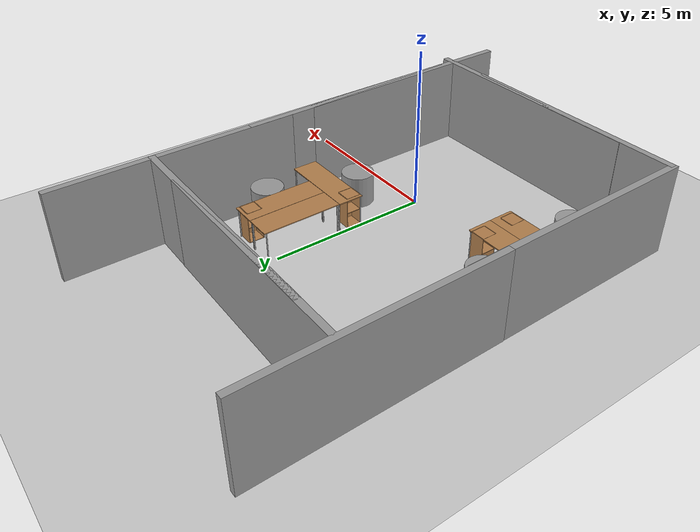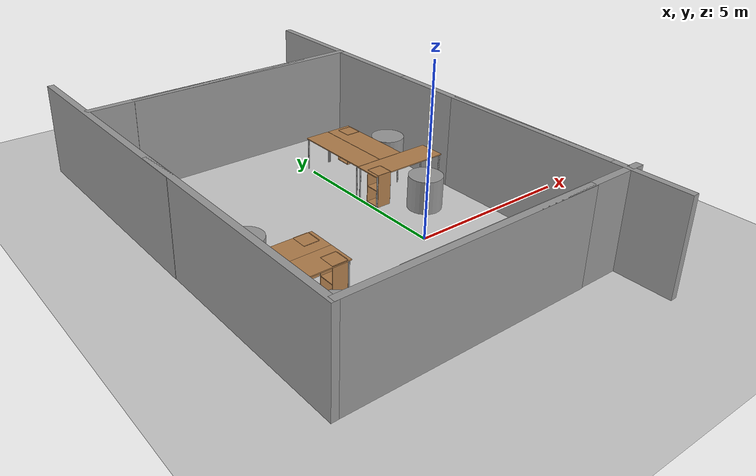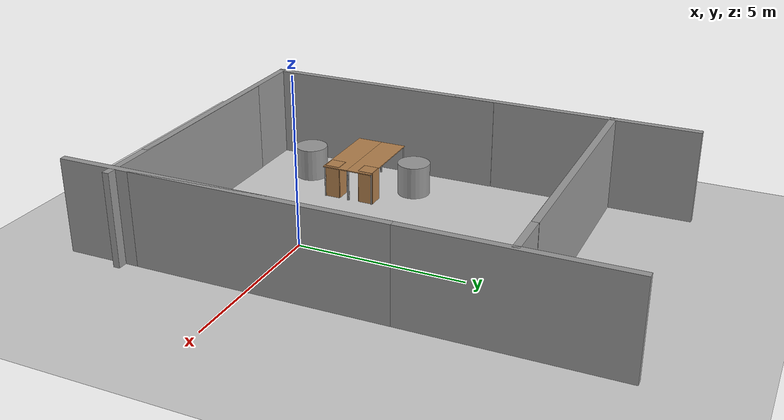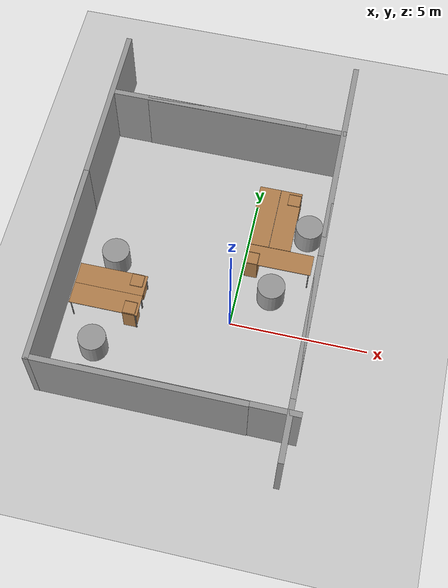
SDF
<sdf version="1.7">
 <world name="default">
  <light name="sun" type="directional">
   <pose>0 0 10 0 -0 0</pose>
   <diffuse>0.8 0.8 0.8 1</diffuse>
   <specular>0.2 0.2 0.2 1</specular>
   <attenuation>
    <range>1000</range>
    <constant>0.9</constant>
    <linear>0.01</linear>
    <quadratic>0.001</quadratic>
   </attenuation>
   <direction>-0.5 0.1 -0.9</direction>
   <spot><inner_angle>0</inner_angle><outer_angle>0</outer_angle><falloff>0</falloff></spot>
  </light>
  <model name="ground_plane">
   <static>1</static>
   <link name="link">
    <collision name="collision">
     <geometry><plane><normal>0 0 1</normal><size>100 100</size></plane></geometry>
     <surface><friction><ode><mu>100</mu><mu2>50</mu2></ode></friction></surface>
    </collision>
    <visual name="visual">
     <cast_shadows>0</cast_shadows>
     <geometry><plane><normal>0 0 1</normal><size>100 100</size></plane></geometry>
     <material>
      <script><uri>file://media/materials/scripts/gazebo.material</uri><name>Gazebo/Grey</name></script>
     </material>
    </visual>
   </link>
  </model>
  <gravity>0 0 -9.8</gravity>
  <magnetic_field>6e-06 2.3e-05 -4.2e-05</magnetic_field>
  <atmosphere type="adiabatic"/>
  <physics type="ode">
   <max_step_size>0.001</max_step_size>
   <real_time_factor>1</real_time_factor>
   <real_time_update_rate>1000</real_time_update_rate>
  </physics>
  <scene><ambient>0.4 0.4 0.4 1</ambient><background>0.7 0.7 0.7 1</background><shadows>1</shadows></scene>
  <audio><device>default</device></audio>
  <spherical_coordinates>
   <surface_model>EARTH_WGS84</surface_model>
   <latitude_deg>0</latitude_deg>
   <longitude_deg>0</longitude_deg>
   <elevation>0</elevation>
   <heading_deg>0</heading_deg>
  </spherical_coordinates>
  <model name="table_office">
   <link name="link">
    <pose>0 0 0 0 -0.001847 0</pose>
    <inertial>
     <mass>1</mass>
     <inertia><ixx>1</ixx><ixy>0</ixy><ixz>0</ixz><iyy>1</iyy><iyz>0</iyz><izz>1</izz></inertia>
    </inertial>
    <visual name="front_right_leg">
     <pose>1.18 -0.38 0.5 0 -0 0</pose>
     <geometry><cylinder><radius>0.02</radius><length>1</length></cylinder></geometry>
     <material>
      <script><uri>file://media/materials/scripts/gazebo.material</uri><name>Gazebo/Grey</name></script>
      <shader type="pixel"><normal_map>__default__</normal_map></shader>
      <ambient>0.3 0.3 0.3 1</ambient>
      <diffuse>0.7 0.7 0.7 1</diffuse>
      <specular>0.01 0.01 0.01 1</specular>
      <emissive>0 0 0 1</emissive>
     </material>
    </visual>
    <visual name="front_left_leg">
     <pose>1.18 0.38 0.5 0 -0 0</pose>
     <geometry><cylinder><radius>0.02</radius><length>1</length></cylinder></geometry>
     <material>
      <script><uri>file://media/materials/scripts/gazebo.material</uri><name>Gazebo/Grey</name></script>
      <shader type="pixel"><normal_map>__default__</normal_map></shader>
      <ambient>0.3 0.3 0.3 1</ambient>
      <diffuse>0.7 0.7 0.7 1</diffuse>
      <specular>0.01 0.01 0.01 1</specular>
      <emissive>0 0 0 1</emissive>
     </material>
    </visual>
    <visual name="back_right_leg">
     <pose>-1.18 -0.38 0.5 0 -0 0</pose>
     <geometry><cylinder><radius>0.02</radius><length>1</length></cylinder></geometry>
     <material>
      <script><uri>file://media/materials/scripts/gazebo.material</uri><name>Gazebo/Grey</name></script>
      <shader type="pixel"><normal_map>__default__</normal_map></shader>
      <ambient>0.3 0.3 0.3 1</ambient>
      <diffuse>0.7 0.7 0.7 1</diffuse>
      <specular>0.01 0.01 0.01 1</specular>
      <emissive>0 0 0 1</emissive>
     </material>
    </visual>
    <visual name="visual1">
     <pose>0 0 1 0 -0 0</pose>
     <geometry><box><size>2.5 0.8 0.03</size></box></geometry>
     <material>
      <script><uri>file://media/materials/scripts/gazebo.material</uri><name>Gazebo/Wood</name></script>
      <shader type="pixel"><normal_map>__default__</normal_map></shader>
      <ambient>1 1 1 1</ambient>
      <diffuse>1 1 1 1</diffuse>
      <specular>0.2 0.2 0.2 1</specular>
      <emissive>0 0 0 1</emissive>
     </material>
    </visual>
    <visual name="back_left_leg">
     <pose>-1.18 0.38 0.5 0 -0 0</pose>
     <geometry><cylinder><radius>0.02</radius><length>1</length></cylinder></geometry>
     <material>
      <script><uri>file://media/materials/scripts/gazebo.material</uri><name>Gazebo/Grey</name></script>
      <shader type="pixel"><normal_map>__default__</normal_map></shader>
      <ambient>0.3 0.3 0.3 1</ambient>
      <diffuse>0.7 0.7 0.7 1</diffuse>
      <specular>0.01 0.01 0.01 1</specular>
      <emissive>0 0 0 1</emissive>
     </material>
    </visual>
    <collision name="back_left_leg">
     <pose>-0.68 0.38 0.5 0 -0 0</pose>
     <geometry><cylinder><radius>0.02</radius><length>1</length></cylinder></geometry>
     <surface>
      <friction>
       <ode><mu>1</mu><mu2>1</mu2><fdir1>0 0 0</fdir1><slip1>0</slip1><slip2>0</slip2></ode>
       <torsional>
        <coefficient>1</coefficient>
        <patch_radius>0</patch_radius>
        <surface_radius>0</surface_radius>
        <use_patch_radius>1</use_patch_radius>
        <ode><slip>0</slip></ode>
       </torsional>
      </friction>
      <bounce><restitution_coefficient>0</restitution_coefficient><threshold>1e+06</threshold></bounce>
      <contact>
       <collide_without_contact>0</collide_without_contact>
       <collide_without_contact_bitmask>1</collide_without_contact_bitmask>
       <collide_bitmask>1</collide_bitmask>
       <ode>
        <soft_cfm>0</soft_cfm>
        <soft_erp>0.2</soft_erp>
        <kp>1e+13</kp>
        <kd>1</kd>
        <max_vel>0.01</max_vel>
        <min_depth>0</min_depth>
       </ode>
       <bullet>
        <split_impulse>1</split_impulse>
        <split_impulse_penetration_threshold>-0.01</split_impulse_penetration_threshold>
        <soft_cfm>0</soft_cfm>
        <soft_erp>0.2</soft_erp>
        <kp>1e+13</kp>
        <kd>1</kd>
       </bullet>
      </contact>
     </surface>
    </collision>
    <collision name="front_right_leg">
     <pose>0.68 -0.38 0.5 0 -0 0</pose>
     <geometry><cylinder><radius>0.02</radius><length>1</length></cylinder></geometry>
     <surface>
      <friction>
       <ode><mu>1</mu><mu2>1</mu2><fdir1>0 0 0</fdir1><slip1>0</slip1><slip2>0</slip2></ode>
       <torsional>
        <coefficient>1</coefficient>
        <patch_radius>0</patch_radius>
        <surface_radius>0</surface_radius>
        <use_patch_radius>1</use_patch_radius>
        <ode><slip>0</slip></ode>
       </torsional>
      </friction>
      <bounce><restitution_coefficient>0</restitution_coefficient><threshold>1e+06</threshold></bounce>
      <contact>
       <collide_without_contact>0</collide_without_contact>
       <collide_without_contact_bitmask>1</collide_without_contact_bitmask>
       <collide_bitmask>1</collide_bitmask>
       <ode>
        <soft_cfm>0</soft_cfm>
        <soft_erp>0.2</soft_erp>
        <kp>1e+13</kp>
        <kd>1</kd>
        <max_vel>0.01</max_vel>
        <min_depth>0</min_depth>
       </ode>
       <bullet>
        <split_impulse>1</split_impulse>
        <split_impulse_penetration_threshold>-0.01</split_impulse_penetration_threshold>
        <soft_cfm>0</soft_cfm>
        <soft_erp>0.2</soft_erp>
        <kp>1e+13</kp>
        <kd>1</kd>
       </bullet>
      </contact>
     </surface>
    </collision>
    <collision name="surface">
     <pose>0 0 1 0 -0 0</pose>
     <geometry><box><size>1.5 0.8 0.03</size></box></geometry>
     <surface>
      <friction>
       <ode><mu>0.6</mu><mu2>0.6</mu2><fdir1>0 0 0</fdir1><slip1>0</slip1><slip2>0</slip2></ode>
       <torsional>
        <coefficient>1</coefficient>
        <patch_radius>0</patch_radius>
        <surface_radius>0</surface_radius>
        <use_patch_radius>1</use_patch_radius>
        <ode><slip>0</slip></ode>
       </torsional>
      </friction>
      <bounce><restitution_coefficient>0</restitution_coefficient><threshold>1e+06</threshold></bounce>
      <contact>
       <collide_without_contact>0</collide_without_contact>
       <collide_without_contact_bitmask>1</collide_without_contact_bitmask>
       <collide_bitmask>1</collide_bitmask>
       <ode>
        <soft_cfm>0</soft_cfm>
        <soft_erp>0.2</soft_erp>
        <kp>1e+13</kp>
        <kd>1</kd>
        <max_vel>0.01</max_vel>
        <min_depth>0</min_depth>
       </ode>
       <bullet>
        <split_impulse>1</split_impulse>
        <split_impulse_penetration_threshold>-0.01</split_impulse_penetration_threshold>
        <soft_cfm>0</soft_cfm>
        <soft_erp>0.2</soft_erp>
        <kp>1e+13</kp>
        <kd>1</kd>
       </bullet>
      </contact>
     </surface>
    </collision>
    <collision name="back_right_leg">
     <pose>-0.68 -0.38 0.5 0 -0 0</pose>
     <geometry><cylinder><radius>0.02</radius><length>1</length></cylinder></geometry>
     <surface>
      <friction>
       <ode><mu>1</mu><mu2>1</mu2><fdir1>0 0 0</fdir1><slip1>0</slip1><slip2>0</slip2></ode>
       <torsional>
        <coefficient>1</coefficient>
        <patch_radius>0</patch_radius>
        <surface_radius>0</surface_radius>
        <use_patch_radius>1</use_patch_radius>
        <ode><slip>0</slip></ode>
       </torsional>
      </friction>
      <bounce><restitution_coefficient>0</restitution_coefficient><threshold>1e+06</threshold></bounce>
      <contact>
       <collide_without_contact>0</collide_without_contact>
       <collide_without_contact_bitmask>1</collide_without_contact_bitmask>
       <collide_bitmask>1</collide_bitmask>
       <ode>
        <soft_cfm>0</soft_cfm>
        <soft_erp>0.2</soft_erp>
        <kp>1e+13</kp>
        <kd>1</kd>
        <max_vel>0.01</max_vel>
        <min_depth>0</min_depth>
       </ode>
       <bullet>
        <split_impulse>1</split_impulse>
        <split_impulse_penetration_threshold>-0.01</split_impulse_penetration_threshold>
        <soft_cfm>0</soft_cfm>
        <soft_erp>0.2</soft_erp>
        <kp>1e+13</kp>
        <kd>1</kd>
       </bullet>
      </contact>
     </surface>
    </collision>
    <collision name="front_left_leg">
     <pose>0.68 0.38 0.5 0 -0 0</pose>
     <geometry><cylinder><radius>0.02</radius><length>1</length></cylinder></geometry>
     <surface>
      <friction>
       <ode><mu>1</mu><mu2>1</mu2><fdir1>0 0 0</fdir1><slip1>0</slip1><slip2>0</slip2></ode>
       <torsional>
        <coefficient>1</coefficient>
        <patch_radius>0</patch_radius>
        <surface_radius>0</surface_radius>
        <use_patch_radius>1</use_patch_radius>
        <ode><slip>0</slip></ode>
       </torsional>
      </friction>
      <bounce><restitution_coefficient>0</restitution_coefficient><threshold>1e+06</threshold></bounce>
      <contact>
       <collide_without_contact>0</collide_without_contact>
       <collide_without_contact_bitmask>1</collide_without_contact_bitmask>
       <collide_bitmask>1</collide_bitmask>
       <ode>
        <soft_cfm>0</soft_cfm>
        <soft_erp>0.2</soft_erp>
        <kp>1e+13</kp>
        <kd>1</kd>
        <max_vel>0.01</max_vel>
        <min_depth>0</min_depth>
       </ode>
       <bullet>
        <split_impulse>1</split_impulse>
        <split_impulse_penetration_threshold>-0.01</split_impulse_penetration_threshold>
        <soft_cfm>0</soft_cfm>
        <soft_erp>0.2</soft_erp>
        <kp>1e+13</kp>
        <kd>1</kd>
       </bullet>
      </contact>
     </surface>
    </collision>
   </link>
   <static>1</static>
   <pose>-4.41652 -0.486154 0 0 -0 0</pose>
  </model>
  <model name="table_office_clone">
   <link name="link">
    <pose>0 0 0 0 -0.001847 0</pose>
    <inertial>
     <mass>1</mass>
     <inertia><ixx>1</ixx><ixy>0</ixy><ixz>0</ixz><iyy>1</iyy><iyz>0</iyz><izz>1</izz></inertia>
    </inertial>
    <visual name="front_right_leg">
     <pose>1.18 -0.38 0.5 0 -0 0</pose>
     <geometry><cylinder><radius>0.02</radius><length>1</length></cylinder></geometry>
     <material>
      <script><uri>file://media/materials/scripts/gazebo.material</uri><name>Gazebo/Grey</name></script>
      <shader type="pixel"><normal_map>__default__</normal_map></shader>
      <ambient>0.3 0.3 0.3 1</ambient>
      <diffuse>0.7 0.7 0.7 1</diffuse>
      <specular>0.01 0.01 0.01 1</specular>
      <emissive>0 0 0 1</emissive>
     </material>
    </visual>
    <visual name="front_left_leg">
     <pose>1.18 0.38 0.5 0 -0 0</pose>
     <geometry><cylinder><radius>0.02</radius><length>1</length></cylinder></geometry>
     <material>
      <script><uri>file://media/materials/scripts/gazebo.material</uri><name>Gazebo/Grey</name></script>
      <shader type="pixel"><normal_map>__default__</normal_map></shader>
      <ambient>0.3 0.3 0.3 1</ambient>
      <diffuse>0.7 0.7 0.7 1</diffuse>
      <specular>0.01 0.01 0.01 1</specular>
      <emissive>0 0 0 1</emissive>
     </material>
    </visual>
    <visual name="back_right_leg">
     <pose>-1.18 -0.38 0.5 0 -0 0</pose>
     <geometry><cylinder><radius>0.02</radius><length>1</length></cylinder></geometry>
     <material>
      <script><uri>file://media/materials/scripts/gazebo.material</uri><name>Gazebo/Grey</name></script>
      <shader type="pixel"><normal_map>__default__</normal_map></shader>
      <ambient>0.3 0.3 0.3 1</ambient>
      <diffuse>0.7 0.7 0.7 1</diffuse>
      <specular>0.01 0.01 0.01 1</specular>
      <emissive>0 0 0 1</emissive>
     </material>
    </visual>
    <visual name="visual1">
     <pose>0 0 1 0 -0 0</pose>
     <geometry><box><size>2.5 0.8 0.03</size></box></geometry>
     <material>
      <script><uri>file://media/materials/scripts/gazebo.material</uri><name>Gazebo/Wood</name></script>
      <shader type="pixel"><normal_map>__default__</normal_map></shader>
      <ambient>1 1 1 1</ambient>
      <diffuse>1 1 1 1</diffuse>
      <specular>0.2 0.2 0.2 1</specular>
      <emissive>0 0 0 1</emissive>
     </material>
    </visual>
    <visual name="back_left_leg">
     <pose>-1.18 0.38 0.5 0 -0 0</pose>
     <geometry><cylinder><radius>0.02</radius><length>1</length></cylinder></geometry>
     <material>
      <script><uri>file://media/materials/scripts/gazebo.material</uri><name>Gazebo/Grey</name></script>
      <shader type="pixel"><normal_map>__default__</normal_map></shader>
      <ambient>0.3 0.3 0.3 1</ambient>
      <diffuse>0.7 0.7 0.7 1</diffuse>
      <specular>0.01 0.01 0.01 1</specular>
      <emissive>0 0 0 1</emissive>
     </material>
    </visual>
    <collision name="back_left_leg">
     <pose>-0.68 0.38 0.5 0 -0 0</pose>
     <geometry><cylinder><radius>0.02</radius><length>1</length></cylinder></geometry>
     <surface>
      <friction>
       <ode><mu>1</mu><mu2>1</mu2><fdir1>0 0 0</fdir1><slip1>0</slip1><slip2>0</slip2></ode>
       <torsional>
        <coefficient>1</coefficient>
        <patch_radius>0</patch_radius>
        <surface_radius>0</surface_radius>
        <use_patch_radius>1</use_patch_radius>
        <ode><slip>0</slip></ode>
       </torsional>
      </friction>
      <bounce><restitution_coefficient>0</restitution_coefficient><threshold>1e+06</threshold></bounce>
      <contact>
       <collide_without_contact>0</collide_without_contact>
       <collide_without_contact_bitmask>1</collide_without_contact_bitmask>
       <collide_bitmask>1</collide_bitmask>
       <ode>
        <soft_cfm>0</soft_cfm>
        <soft_erp>0.2</soft_erp>
        <kp>1e+13</kp>
        <kd>1</kd>
        <max_vel>0.01</max_vel>
        <min_depth>0</min_depth>
       </ode>
       <bullet>
        <split_impulse>1</split_impulse>
        <split_impulse_penetration_threshold>-0.01</split_impulse_penetration_threshold>
        <soft_cfm>0</soft_cfm>
        <soft_erp>0.2</soft_erp>
        <kp>1e+13</kp>
        <kd>1</kd>
       </bullet>
      </contact>
     </surface>
    </collision>
    <collision name="front_right_leg">
     <pose>0.68 -0.38 0.5 0 -0 0</pose>
     <geometry><cylinder><radius>0.02</radius><length>1</length></cylinder></geometry>
     <surface>
      <friction>
       <ode><mu>1</mu><mu2>1</mu2><fdir1>0 0 0</fdir1><slip1>0</slip1><slip2>0</slip2></ode>
       <torsional>
        <coefficient>1</coefficient>
        <patch_radius>0</patch_radius>
        <surface_radius>0</surface_radius>
        <use_patch_radius>1</use_patch_radius>
        <ode><slip>0</slip></ode>
       </torsional>
      </friction>
      <bounce><restitution_coefficient>0</restitution_coefficient><threshold>1e+06</threshold></bounce>
      <contact>
       <collide_without_contact>0</collide_without_contact>
       <collide_without_contact_bitmask>1</collide_without_contact_bitmask>
       <collide_bitmask>1</collide_bitmask>
       <ode>
        <soft_cfm>0</soft_cfm>
        <soft_erp>0.2</soft_erp>
        <kp>1e+13</kp>
        <kd>1</kd>
        <max_vel>0.01</max_vel>
        <min_depth>0</min_depth>
       </ode>
       <bullet>
        <split_impulse>1</split_impulse>
        <split_impulse_penetration_threshold>-0.01</split_impulse_penetration_threshold>
        <soft_cfm>0</soft_cfm>
        <soft_erp>0.2</soft_erp>
        <kp>1e+13</kp>
        <kd>1</kd>
       </bullet>
      </contact>
     </surface>
    </collision>
    <collision name="surface">
     <pose>0 0 1 0 -0 0</pose>
     <geometry><box><size>1.5 0.8 0.03</size></box></geometry>
     <surface>
      <friction>
       <ode><mu>0.6</mu><mu2>0.6</mu2><fdir1>0 0 0</fdir1><slip1>0</slip1><slip2>0</slip2></ode>
       <torsional>
        <coefficient>1</coefficient>
        <patch_radius>0</patch_radius>
        <surface_radius>0</surface_radius>
        <use_patch_radius>1</use_patch_radius>
        <ode><slip>0</slip></ode>
       </torsional>
      </friction>
      <bounce><restitution_coefficient>0</restitution_coefficient><threshold>1e+06</threshold></bounce>
      <contact>
       <collide_without_contact>0</collide_without_contact>
       <collide_without_contact_bitmask>1</collide_without_contact_bitmask>
       <collide_bitmask>1</collide_bitmask>
       <ode>
        <soft_cfm>0</soft_cfm>
        <soft_erp>0.2</soft_erp>
        <kp>1e+13</kp>
        <kd>1</kd>
        <max_vel>0.01</max_vel>
        <min_depth>0</min_depth>
       </ode>
       <bullet>
        <split_impulse>1</split_impulse>
        <split_impulse_penetration_threshold>-0.01</split_impulse_penetration_threshold>
        <soft_cfm>0</soft_cfm>
        <soft_erp>0.2</soft_erp>
        <kp>1e+13</kp>
        <kd>1</kd>
       </bullet>
      </contact>
     </surface>
    </collision>
    <collision name="back_right_leg">
     <pose>-0.68 -0.38 0.5 0 -0 0</pose>
     <geometry><cylinder><radius>0.02</radius><length>1</length></cylinder></geometry>
     <surface>
      <friction>
       <ode><mu>1</mu><mu2>1</mu2><fdir1>0 0 0</fdir1><slip1>0</slip1><slip2>0</slip2></ode>
       <torsional>
        <coefficient>1</coefficient>
        <patch_radius>0</patch_radius>
        <surface_radius>0</surface_radius>
        <use_patch_radius>1</use_patch_radius>
        <ode><slip>0</slip></ode>
       </torsional>
      </friction>
      <bounce><restitution_coefficient>0</restitution_coefficient><threshold>1e+06</threshold></bounce>
      <contact>
       <collide_without_contact>0</collide_without_contact>
       <collide_without_contact_bitmask>1</collide_without_contact_bitmask>
       <collide_bitmask>1</collide_bitmask>
       <ode>
        <soft_cfm>0</soft_cfm>
        <soft_erp>0.2</soft_erp>
        <kp>1e+13</kp>
        <kd>1</kd>
        <max_vel>0.01</max_vel>
        <min_depth>0</min_depth>
       </ode>
       <bullet>
        <split_impulse>1</split_impulse>
        <split_impulse_penetration_threshold>-0.01</split_impulse_penetration_threshold>
        <soft_cfm>0</soft_cfm>
        <soft_erp>0.2</soft_erp>
        <kp>1e+13</kp>
        <kd>1</kd>
       </bullet>
      </contact>
     </surface>
    </collision>
    <collision name="front_left_leg">
     <pose>0.68 0.38 0.5 0 -0 0</pose>
     <geometry><cylinder><radius>0.02</radius><length>1</length></cylinder></geometry>
     <surface>
      <friction>
       <ode><mu>1</mu><mu2>1</mu2><fdir1>0 0 0</fdir1><slip1>0</slip1><slip2>0</slip2></ode>
       <torsional>
        <coefficient>1</coefficient>
        <patch_radius>0</patch_radius>
        <surface_radius>0</surface_radius>
        <use_patch_radius>1</use_patch_radius>
        <ode><slip>0</slip></ode>
       </torsional>
      </friction>
      <bounce><restitution_coefficient>0</restitution_coefficient><threshold>1e+06</threshold></bounce>
      <contact>
       <collide_without_contact>0</collide_without_contact>
       <collide_without_contact_bitmask>1</collide_without_contact_bitmask>
       <collide_bitmask>1</collide_bitmask>
       <ode>
        <soft_cfm>0</soft_cfm>
        <soft_erp>0.2</soft_erp>
        <kp>1e+13</kp>
        <kd>1</kd>
        <max_vel>0.01</max_vel>
        <min_depth>0</min_depth>
       </ode>
       <bullet>
        <split_impulse>1</split_impulse>
        <split_impulse_penetration_threshold>-0.01</split_impulse_penetration_threshold>
        <soft_cfm>0</soft_cfm>
        <soft_erp>0.2</soft_erp>
        <kp>1e+13</kp>
        <kd>1</kd>
       </bullet>
      </contact>
     </surface>
    </collision>
   </link>
   <static>1</static>
   <pose>-4.41737 0.311441 0 0 -0 0</pose>
  </model>
  <model name="table_office_clone_clone">
   <link name="link">
    <pose>0 0 0 0 -0.001847 0</pose>
    <inertial>
     <mass>1</mass>
     <inertia><ixx>1</ixx><ixy>0</ixy><ixz>0</ixz><iyy>1</iyy><iyz>0</iyz><izz>1</izz></inertia>
    </inertial>
    <visual name="front_right_leg">
     <pose>1.18 -0.38 0.5 0 -0 0</pose>
     <geometry><cylinder><radius>0.02</radius><length>1</length></cylinder></geometry>
     <material>
      <script><uri>file://media/materials/scripts/gazebo.material</uri><name>Gazebo/Grey</name></script>
      <shader type="pixel"><normal_map>__default__</normal_map></shader>
      <ambient>0.3 0.3 0.3 1</ambient>
      <diffuse>0.7 0.7 0.7 1</diffuse>
      <specular>0.01 0.01 0.01 1</specular>
      <emissive>0 0 0 1</emissive>
     </material>
    </visual>
    <visual name="front_left_leg">
     <pose>1.18 0.38 0.5 0 -0 0</pose>
     <geometry><cylinder><radius>0.02</radius><length>1</length></cylinder></geometry>
     <material>
      <script><uri>file://media/materials/scripts/gazebo.material</uri><name>Gazebo/Grey</name></script>
      <shader type="pixel"><normal_map>__default__</normal_map></shader>
      <ambient>0.3 0.3 0.3 1</ambient>
      <diffuse>0.7 0.7 0.7 1</diffuse>
      <specular>0.01 0.01 0.01 1</specular>
      <emissive>0 0 0 1</emissive>
     </material>
    </visual>
    <visual name="back_right_leg">
     <pose>-1.18 -0.38 0.5 0 -0 0</pose>
     <geometry><cylinder><radius>0.02</radius><length>1</length></cylinder></geometry>
     <material>
      <script><uri>file://media/materials/scripts/gazebo.material</uri><name>Gazebo/Grey</name></script>
      <shader type="pixel"><normal_map>__default__</normal_map></shader>
      <ambient>0.3 0.3 0.3 1</ambient>
      <diffuse>0.7 0.7 0.7 1</diffuse>
      <specular>0.01 0.01 0.01 1</specular>
      <emissive>0 0 0 1</emissive>
     </material>
    </visual>
    <visual name="visual1">
     <pose>0 0 1 0 -0 0</pose>
     <geometry><box><size>2.5 0.8 0.03</size></box></geometry>
     <material>
      <script><uri>file://media/materials/scripts/gazebo.material</uri><name>Gazebo/Wood</name></script>
      <shader type="pixel"><normal_map>__default__</normal_map></shader>
      <ambient>1 1 1 1</ambient>
      <diffuse>1 1 1 1</diffuse>
      <specular>0.2 0.2 0.2 1</specular>
      <emissive>0 0 0 1</emissive>
     </material>
    </visual>
    <visual name="back_left_leg">
     <pose>-1.18 0.38 0.5 0 -0 0</pose>
     <geometry><cylinder><radius>0.02</radius><length>1</length></cylinder></geometry>
     <material>
      <script><uri>file://media/materials/scripts/gazebo.material</uri><name>Gazebo/Grey</name></script>
      <shader type="pixel"><normal_map>__default__</normal_map></shader>
      <ambient>0.3 0.3 0.3 1</ambient>
      <diffuse>0.7 0.7 0.7 1</diffuse>
      <specular>0.01 0.01 0.01 1</specular>
      <emissive>0 0 0 1</emissive>
     </material>
    </visual>
    <collision name="back_left_leg">
     <pose>-0.68 0.38 0.5 0 -0 0</pose>
     <geometry><cylinder><radius>0.02</radius><length>1</length></cylinder></geometry>
     <surface>
      <friction>
       <ode><mu>1</mu><mu2>1</mu2><fdir1>0 0 0</fdir1><slip1>0</slip1><slip2>0</slip2></ode>
       <torsional>
        <coefficient>1</coefficient>
        <patch_radius>0</patch_radius>
        <surface_radius>0</surface_radius>
        <use_patch_radius>1</use_patch_radius>
        <ode><slip>0</slip></ode>
       </torsional>
      </friction>
      <bounce><restitution_coefficient>0</restitution_coefficient><threshold>1e+06</threshold></bounce>
      <contact>
       <collide_without_contact>0</collide_without_contact>
       <collide_without_contact_bitmask>1</collide_without_contact_bitmask>
       <collide_bitmask>1</collide_bitmask>
       <ode>
        <soft_cfm>0</soft_cfm>
        <soft_erp>0.2</soft_erp>
        <kp>1e+13</kp>
        <kd>1</kd>
        <max_vel>0.01</max_vel>
        <min_depth>0</min_depth>
       </ode>
       <bullet>
        <split_impulse>1</split_impulse>
        <split_impulse_penetration_threshold>-0.01</split_impulse_penetration_threshold>
        <soft_cfm>0</soft_cfm>
        <soft_erp>0.2</soft_erp>
        <kp>1e+13</kp>
        <kd>1</kd>
       </bullet>
      </contact>
     </surface>
    </collision>
    <collision name="front_right_leg">
     <pose>0.68 -0.38 0.5 0 -0 0</pose>
     <geometry><cylinder><radius>0.02</radius><length>1</length></cylinder></geometry>
     <surface>
      <friction>
       <ode><mu>1</mu><mu2>1</mu2><fdir1>0 0 0</fdir1><slip1>0</slip1><slip2>0</slip2></ode>
       <torsional>
        <coefficient>1</coefficient>
        <patch_radius>0</patch_radius>
        <surface_radius>0</surface_radius>
        <use_patch_radius>1</use_patch_radius>
        <ode><slip>0</slip></ode>
       </torsional>
      </friction>
      <bounce><restitution_coefficient>0</restitution_coefficient><threshold>1e+06</threshold></bounce>
      <contact>
       <collide_without_contact>0</collide_without_contact>
       <collide_without_contact_bitmask>1</collide_without_contact_bitmask>
       <collide_bitmask>1</collide_bitmask>
       <ode>
        <soft_cfm>0</soft_cfm>
        <soft_erp>0.2</soft_erp>
        <kp>1e+13</kp>
        <kd>1</kd>
        <max_vel>0.01</max_vel>
        <min_depth>0</min_depth>
       </ode>
       <bullet>
        <split_impulse>1</split_impulse>
        <split_impulse_penetration_threshold>-0.01</split_impulse_penetration_threshold>
        <soft_cfm>0</soft_cfm>
        <soft_erp>0.2</soft_erp>
        <kp>1e+13</kp>
        <kd>1</kd>
       </bullet>
      </contact>
     </surface>
    </collision>
    <collision name="surface">
     <pose>0 0 1 0 -0 0</pose>
     <geometry><box><size>1.5 0.8 0.03</size></box></geometry>
     <surface>
      <friction>
       <ode><mu>0.6</mu><mu2>0.6</mu2><fdir1>0 0 0</fdir1><slip1>0</slip1><slip2>0</slip2></ode>
       <torsional>
        <coefficient>1</coefficient>
        <patch_radius>0</patch_radius>
        <surface_radius>0</surface_radius>
        <use_patch_radius>1</use_patch_radius>
        <ode><slip>0</slip></ode>
       </torsional>
      </friction>
      <bounce><restitution_coefficient>0</restitution_coefficient><threshold>1e+06</threshold></bounce>
      <contact>
       <collide_without_contact>0</collide_without_contact>
       <collide_without_contact_bitmask>1</collide_without_contact_bitmask>
       <collide_bitmask>1</collide_bitmask>
       <ode>
        <soft_cfm>0</soft_cfm>
        <soft_erp>0.2</soft_erp>
        <kp>1e+13</kp>
        <kd>1</kd>
        <max_vel>0.01</max_vel>
        <min_depth>0</min_depth>
       </ode>
       <bullet>
        <split_impulse>1</split_impulse>
        <split_impulse_penetration_threshold>-0.01</split_impulse_penetration_threshold>
        <soft_cfm>0</soft_cfm>
        <soft_erp>0.2</soft_erp>
        <kp>1e+13</kp>
        <kd>1</kd>
       </bullet>
      </contact>
     </surface>
    </collision>
    <collision name="back_right_leg">
     <pose>-0.68 -0.38 0.5 0 -0 0</pose>
     <geometry><cylinder><radius>0.02</radius><length>1</length></cylinder></geometry>
     <surface>
      <friction>
       <ode><mu>1</mu><mu2>1</mu2><fdir1>0 0 0</fdir1><slip1>0</slip1><slip2>0</slip2></ode>
       <torsional>
        <coefficient>1</coefficient>
        <patch_radius>0</patch_radius>
        <surface_radius>0</surface_radius>
        <use_patch_radius>1</use_patch_radius>
        <ode><slip>0</slip></ode>
       </torsional>
      </friction>
      <bounce><restitution_coefficient>0</restitution_coefficient><threshold>1e+06</threshold></bounce>
      <contact>
       <collide_without_contact>0</collide_without_contact>
       <collide_without_contact_bitmask>1</collide_without_contact_bitmask>
       <collide_bitmask>1</collide_bitmask>
       <ode>
        <soft_cfm>0</soft_cfm>
        <soft_erp>0.2</soft_erp>
        <kp>1e+13</kp>
        <kd>1</kd>
        <max_vel>0.01</max_vel>
        <min_depth>0</min_depth>
       </ode>
       <bullet>
        <split_impulse>1</split_impulse>
        <split_impulse_penetration_threshold>-0.01</split_impulse_penetration_threshold>
        <soft_cfm>0</soft_cfm>
        <soft_erp>0.2</soft_erp>
        <kp>1e+13</kp>
        <kd>1</kd>
       </bullet>
      </contact>
     </surface>
    </collision>
    <collision name="front_left_leg">
     <pose>0.68 0.38 0.5 0 -0 0</pose>
     <geometry><cylinder><radius>0.02</radius><length>1</length></cylinder></geometry>
     <surface>
      <friction>
       <ode><mu>1</mu><mu2>1</mu2><fdir1>0 0 0</fdir1><slip1>0</slip1><slip2>0</slip2></ode>
       <torsional>
        <coefficient>1</coefficient>
        <patch_radius>0</patch_radius>
        <surface_radius>0</surface_radius>
        <use_patch_radius>1</use_patch_radius>
        <ode><slip>0</slip></ode>
       </torsional>
      </friction>
      <bounce><restitution_coefficient>0</restitution_coefficient><threshold>1e+06</threshold></bounce>
      <contact>
       <collide_without_contact>0</collide_without_contact>
       <collide_without_contact_bitmask>1</collide_without_contact_bitmask>
       <collide_bitmask>1</collide_bitmask>
       <ode>
        <soft_cfm>0</soft_cfm>
        <soft_erp>0.2</soft_erp>
        <kp>1e+13</kp>
        <kd>1</kd>
        <max_vel>0.01</max_vel>
        <min_depth>0</min_depth>
       </ode>
       <bullet>
        <split_impulse>1</split_impulse>
        <split_impulse_penetration_threshold>-0.01</split_impulse_penetration_threshold>
        <soft_cfm>0</soft_cfm>
        <soft_erp>0.2</soft_erp>
        <kp>1e+13</kp>
        <kd>1</kd>
       </bullet>
      </contact>
     </surface>
    </collision>
   </link>
   <static>1</static>
   <pose>1.25466 2.44122 0 0 -0 0</pose>
  </model>
  <model name="table_office_clone_clone_clone_clone">
   <link name="link">
    <pose>0 0 0 0 -0.001847 0</pose>
    <inertial>
     <mass>1</mass>
     <inertia><ixx>1</ixx><ixy>0</ixy><ixz>0</ixz><iyy>1</iyy><iyz>0</iyz><izz>1</izz></inertia>
    </inertial>
    <visual name="front_right_leg">
     <pose>1.18 -0.38 0.5 0 -0 0</pose>
     <geometry><cylinder><radius>0.02</radius><length>1</length></cylinder></geometry>
     <material>
      <script><uri>file://media/materials/scripts/gazebo.material</uri><name>Gazebo/Grey</name></script>
      <shader type="pixel"><normal_map>__default__</normal_map></shader>
      <ambient>0.3 0.3 0.3 1</ambient>
      <diffuse>0.7 0.7 0.7 1</diffuse>
      <specular>0.01 0.01 0.01 1</specular>
      <emissive>0 0 0 1</emissive>
     </material>
    </visual>
    <visual name="front_left_leg">
     <pose>1.18 0.38 0.5 0 -0 0</pose>
     <geometry><cylinder><radius>0.02</radius><length>1</length></cylinder></geometry>
     <material>
      <script><uri>file://media/materials/scripts/gazebo.material</uri><name>Gazebo/Grey</name></script>
      <shader type="pixel"><normal_map>__default__</normal_map></shader>
      <ambient>0.3 0.3 0.3 1</ambient>
      <diffuse>0.7 0.7 0.7 1</diffuse>
      <specular>0.01 0.01 0.01 1</specular>
      <emissive>0 0 0 1</emissive>
     </material>
    </visual>
    <visual name="back_right_leg">
     <pose>-1.18 -0.38 0.5 0 -0 0</pose>
     <geometry><cylinder><radius>0.02</radius><length>1</length></cylinder></geometry>
     <material>
      <script><uri>file://media/materials/scripts/gazebo.material</uri><name>Gazebo/Grey</name></script>
      <shader type="pixel"><normal_map>__default__</normal_map></shader>
      <ambient>0.3 0.3 0.3 1</ambient>
      <diffuse>0.7 0.7 0.7 1</diffuse>
      <specular>0.01 0.01 0.01 1</specular>
      <emissive>0 0 0 1</emissive>
     </material>
    </visual>
    <visual name="visual1">
     <pose>0 0 1 0 -0 0</pose>
     <geometry><box><size>2.5 0.8 0.03</size></box></geometry>
     <material>
      <script><uri>file://media/materials/scripts/gazebo.material</uri><name>Gazebo/Wood</name></script>
      <shader type="pixel"><normal_map>__default__</normal_map></shader>
      <ambient>1 1 1 1</ambient>
      <diffuse>1 1 1 1</diffuse>
      <specular>0.2 0.2 0.2 1</specular>
      <emissive>0 0 0 1</emissive>
     </material>
    </visual>
    <visual name="back_left_leg">
     <pose>-1.18 0.38 0.5 0 -0 0</pose>
     <geometry><cylinder><radius>0.02</radius><length>1</length></cylinder></geometry>
     <material>
      <script><uri>file://media/materials/scripts/gazebo.material</uri><name>Gazebo/Grey</name></script>
      <shader type="pixel"><normal_map>__default__</normal_map></shader>
      <ambient>0.3 0.3 0.3 1</ambient>
      <diffuse>0.7 0.7 0.7 1</diffuse>
      <specular>0.01 0.01 0.01 1</specular>
      <emissive>0 0 0 1</emissive>
     </material>
    </visual>
    <collision name="back_left_leg">
     <pose>-0.68 0.38 0.5 0 -0 0</pose>
     <geometry><cylinder><radius>0.02</radius><length>1</length></cylinder></geometry>
     <surface>
      <friction>
       <ode><mu>1</mu><mu2>1</mu2><fdir1>0 0 0</fdir1><slip1>0</slip1><slip2>0</slip2></ode>
       <torsional>
        <coefficient>1</coefficient>
        <patch_radius>0</patch_radius>
        <surface_radius>0</surface_radius>
        <use_patch_radius>1</use_patch_radius>
        <ode><slip>0</slip></ode>
       </torsional>
      </friction>
      <bounce><restitution_coefficient>0</restitution_coefficient><threshold>1e+06</threshold></bounce>
      <contact>
       <collide_without_contact>0</collide_without_contact>
       <collide_without_contact_bitmask>1</collide_without_contact_bitmask>
       <collide_bitmask>1</collide_bitmask>
       <ode>
        <soft_cfm>0</soft_cfm>
        <soft_erp>0.2</soft_erp>
        <kp>1e+13</kp>
        <kd>1</kd>
        <max_vel>0.01</max_vel>
        <min_depth>0</min_depth>
       </ode>
       <bullet>
        <split_impulse>1</split_impulse>
        <split_impulse_penetration_threshold>-0.01</split_impulse_penetration_threshold>
        <soft_cfm>0</soft_cfm>
        <soft_erp>0.2</soft_erp>
        <kp>1e+13</kp>
        <kd>1</kd>
       </bullet>
      </contact>
     </surface>
    </collision>
    <collision name="front_right_leg">
     <pose>0.68 -0.38 0.5 0 -0 0</pose>
     <geometry><cylinder><radius>0.02</radius><length>1</length></cylinder></geometry>
     <surface>
      <friction>
       <ode><mu>1</mu><mu2>1</mu2><fdir1>0 0 0</fdir1><slip1>0</slip1><slip2>0</slip2></ode>
       <torsional>
        <coefficient>1</coefficient>
        <patch_radius>0</patch_radius>
        <surface_radius>0</surface_radius>
        <use_patch_radius>1</use_patch_radius>
        <ode><slip>0</slip></ode>
       </torsional>
      </friction>
      <bounce><restitution_coefficient>0</restitution_coefficient><threshold>1e+06</threshold></bounce>
      <contact>
       <collide_without_contact>0</collide_without_contact>
       <collide_without_contact_bitmask>1</collide_without_contact_bitmask>
       <collide_bitmask>1</collide_bitmask>
       <ode>
        <soft_cfm>0</soft_cfm>
        <soft_erp>0.2</soft_erp>
        <kp>1e+13</kp>
        <kd>1</kd>
        <max_vel>0.01</max_vel>
        <min_depth>0</min_depth>
       </ode>
       <bullet>
        <split_impulse>1</split_impulse>
        <split_impulse_penetration_threshold>-0.01</split_impulse_penetration_threshold>
        <soft_cfm>0</soft_cfm>
        <soft_erp>0.2</soft_erp>
        <kp>1e+13</kp>
        <kd>1</kd>
       </bullet>
      </contact>
     </surface>
    </collision>
    <collision name="surface">
     <pose>0 0 1 0 -0 0</pose>
     <geometry><box><size>1.5 0.8 0.03</size></box></geometry>
     <surface>
      <friction>
       <ode><mu>0.6</mu><mu2>0.6</mu2><fdir1>0 0 0</fdir1><slip1>0</slip1><slip2>0</slip2></ode>
       <torsional>
        <coefficient>1</coefficient>
        <patch_radius>0</patch_radius>
        <surface_radius>0</surface_radius>
        <use_patch_radius>1</use_patch_radius>
        <ode><slip>0</slip></ode>
       </torsional>
      </friction>
      <bounce><restitution_coefficient>0</restitution_coefficient><threshold>1e+06</threshold></bounce>
      <contact>
       <collide_without_contact>0</collide_without_contact>
       <collide_without_contact_bitmask>1</collide_without_contact_bitmask>
       <collide_bitmask>1</collide_bitmask>
       <ode>
        <soft_cfm>0</soft_cfm>
        <soft_erp>0.2</soft_erp>
        <kp>1e+13</kp>
        <kd>1</kd>
        <max_vel>0.01</max_vel>
        <min_depth>0</min_depth>
       </ode>
       <bullet>
        <split_impulse>1</split_impulse>
        <split_impulse_penetration_threshold>-0.01</split_impulse_penetration_threshold>
        <soft_cfm>0</soft_cfm>
        <soft_erp>0.2</soft_erp>
        <kp>1e+13</kp>
        <kd>1</kd>
       </bullet>
      </contact>
     </surface>
    </collision>
    <collision name="back_right_leg">
     <pose>-0.68 -0.38 0.5 0 -0 0</pose>
     <geometry><cylinder><radius>0.02</radius><length>1</length></cylinder></geometry>
     <surface>
      <friction>
       <ode><mu>1</mu><mu2>1</mu2><fdir1>0 0 0</fdir1><slip1>0</slip1><slip2>0</slip2></ode>
       <torsional>
        <coefficient>1</coefficient>
        <patch_radius>0</patch_radius>
        <surface_radius>0</surface_radius>
        <use_patch_radius>1</use_patch_radius>
        <ode><slip>0</slip></ode>
       </torsional>
      </friction>
      <bounce><restitution_coefficient>0</restitution_coefficient><threshold>1e+06</threshold></bounce>
      <contact>
       <collide_without_contact>0</collide_without_contact>
       <collide_without_contact_bitmask>1</collide_without_contact_bitmask>
       <collide_bitmask>1</collide_bitmask>
       <ode>
        <soft_cfm>0</soft_cfm>
        <soft_erp>0.2</soft_erp>
        <kp>1e+13</kp>
        <kd>1</kd>
        <max_vel>0.01</max_vel>
        <min_depth>0</min_depth>
       </ode>
       <bullet>
        <split_impulse>1</split_impulse>
        <split_impulse_penetration_threshold>-0.01</split_impulse_penetration_threshold>
        <soft_cfm>0</soft_cfm>
        <soft_erp>0.2</soft_erp>
        <kp>1e+13</kp>
        <kd>1</kd>
       </bullet>
      </contact>
     </surface>
    </collision>
    <collision name="front_left_leg">
     <pose>0.68 0.38 0.5 0 -0 0</pose>
     <geometry><cylinder><radius>0.02</radius><length>1</length></cylinder></geometry>
     <surface>
      <friction>
       <ode><mu>1</mu><mu2>1</mu2><fdir1>0 0 0</fdir1><slip1>0</slip1><slip2>0</slip2></ode>
       <torsional>
        <coefficient>1</coefficient>
        <patch_radius>0</patch_radius>
        <surface_radius>0</surface_radius>
        <use_patch_radius>1</use_patch_radius>
        <ode><slip>0</slip></ode>
       </torsional>
      </friction>
      <bounce><restitution_coefficient>0</restitution_coefficient><threshold>1e+06</threshold></bounce>
      <contact>
       <collide_without_contact>0</collide_without_contact>
       <collide_without_contact_bitmask>1</collide_without_contact_bitmask>
       <collide_bitmask>1</collide_bitmask>
       <ode>
        <soft_cfm>0</soft_cfm>
        <soft_erp>0.2</soft_erp>
        <kp>1e+13</kp>
        <kd>1</kd>
        <max_vel>0.01</max_vel>
        <min_depth>0</min_depth>
       </ode>
       <bullet>
        <split_impulse>1</split_impulse>
        <split_impulse_penetration_threshold>-0.01</split_impulse_penetration_threshold>
        <soft_cfm>0</soft_cfm>
        <soft_erp>0.2</soft_erp>
        <kp>1e+13</kp>
        <kd>1</kd>
       </bullet>
      </contact>
     </surface>
    </collision>
   </link>
   <static>1</static>
   <pose>0.403324 4.09957 0 0 0 -1.56652</pose>
  </model>
  <model name="table_office_clone_clone_clone_clone_0">
   <link name="link">
    <pose>0 0 0 0 -0.001847 0</pose>
    <inertial>
     <mass>1</mass>
     <inertia><ixx>1</ixx><ixy>0</ixy><ixz>0</ixz><iyy>1</iyy><iyz>0</iyz><izz>1</izz></inertia>
    </inertial>
    <visual name="front_right_leg">
     <pose>1.18 -0.38 0.5 0 -0 0</pose>
     <geometry><cylinder><radius>0.02</radius><length>1</length></cylinder></geometry>
     <material>
      <script><uri>file://media/materials/scripts/gazebo.material</uri><name>Gazebo/Grey</name></script>
      <shader type="pixel"><normal_map>__default__</normal_map></shader>
      <ambient>0.3 0.3 0.3 1</ambient>
      <diffuse>0.7 0.7 0.7 1</diffuse>
      <specular>0.01 0.01 0.01 1</specular>
      <emissive>0 0 0 1</emissive>
     </material>
    </visual>
    <visual name="front_left_leg">
     <pose>1.18 0.38 0.5 0 -0 0</pose>
     <geometry><cylinder><radius>0.02</radius><length>1</length></cylinder></geometry>
     <material>
      <script><uri>file://media/materials/scripts/gazebo.material</uri><name>Gazebo/Grey</name></script>
      <shader type="pixel"><normal_map>__default__</normal_map></shader>
      <ambient>0.3 0.3 0.3 1</ambient>
      <diffuse>0.7 0.7 0.7 1</diffuse>
      <specular>0.01 0.01 0.01 1</specular>
      <emissive>0 0 0 1</emissive>
     </material>
    </visual>
    <visual name="back_right_leg">
     <pose>-1.18 -0.38 0.5 0 -0 0</pose>
     <geometry><cylinder><radius>0.02</radius><length>1</length></cylinder></geometry>
     <material>
      <script><uri>file://media/materials/scripts/gazebo.material</uri><name>Gazebo/Grey</name></script>
      <shader type="pixel"><normal_map>__default__</normal_map></shader>
      <ambient>0.3 0.3 0.3 1</ambient>
      <diffuse>0.7 0.7 0.7 1</diffuse>
      <specular>0.01 0.01 0.01 1</specular>
      <emissive>0 0 0 1</emissive>
     </material>
    </visual>
    <visual name="visual1">
     <pose>0 0 1 0 -0 0</pose>
     <geometry><box><size>2.5 0.8 0.03</size></box></geometry>
     <material>
      <script><uri>file://media/materials/scripts/gazebo.material</uri><name>Gazebo/Wood</name></script>
      <shader type="pixel"><normal_map>__default__</normal_map></shader>
      <ambient>1 1 1 1</ambient>
      <diffuse>1 1 1 1</diffuse>
      <specular>0.2 0.2 0.2 1</specular>
      <emissive>0 0 0 1</emissive>
     </material>
    </visual>
    <visual name="back_left_leg">
     <pose>-1.18 0.38 0.5 0 -0 0</pose>
     <geometry><cylinder><radius>0.02</radius><length>1</length></cylinder></geometry>
     <material>
      <script><uri>file://media/materials/scripts/gazebo.material</uri><name>Gazebo/Grey</name></script>
      <shader type="pixel"><normal_map>__default__</normal_map></shader>
      <ambient>0.3 0.3 0.3 1</ambient>
      <diffuse>0.7 0.7 0.7 1</diffuse>
      <specular>0.01 0.01 0.01 1</specular>
      <emissive>0 0 0 1</emissive>
     </material>
    </visual>
    <collision name="back_left_leg">
     <pose>-0.68 0.38 0.5 0 -0 0</pose>
     <geometry><cylinder><radius>0.02</radius><length>1</length></cylinder></geometry>
     <surface>
      <friction>
       <ode><mu>1</mu><mu2>1</mu2><fdir1>0 0 0</fdir1><slip1>0</slip1><slip2>0</slip2></ode>
       <torsional>
        <coefficient>1</coefficient>
        <patch_radius>0</patch_radius>
        <surface_radius>0</surface_radius>
        <use_patch_radius>1</use_patch_radius>
        <ode><slip>0</slip></ode>
       </torsional>
      </friction>
      <bounce><restitution_coefficient>0</restitution_coefficient><threshold>1e+06</threshold></bounce>
      <contact>
       <collide_without_contact>0</collide_without_contact>
       <collide_without_contact_bitmask>1</collide_without_contact_bitmask>
       <collide_bitmask>1</collide_bitmask>
       <ode>
        <soft_cfm>0</soft_cfm>
        <soft_erp>0.2</soft_erp>
        <kp>1e+13</kp>
        <kd>1</kd>
        <max_vel>0.01</max_vel>
        <min_depth>0</min_depth>
       </ode>
       <bullet>
        <split_impulse>1</split_impulse>
        <split_impulse_penetration_threshold>-0.01</split_impulse_penetration_threshold>
        <soft_cfm>0</soft_cfm>
        <soft_erp>0.2</soft_erp>
        <kp>1e+13</kp>
        <kd>1</kd>
       </bullet>
      </contact>
     </surface>
    </collision>
    <collision name="front_right_leg">
     <pose>0.68 -0.38 0.5 0 -0 0</pose>
     <geometry><cylinder><radius>0.02</radius><length>1</length></cylinder></geometry>
     <surface>
      <friction>
       <ode><mu>1</mu><mu2>1</mu2><fdir1>0 0 0</fdir1><slip1>0</slip1><slip2>0</slip2></ode>
       <torsional>
        <coefficient>1</coefficient>
        <patch_radius>0</patch_radius>
        <surface_radius>0</surface_radius>
        <use_patch_radius>1</use_patch_radius>
        <ode><slip>0</slip></ode>
       </torsional>
      </friction>
      <bounce><restitution_coefficient>0</restitution_coefficient><threshold>1e+06</threshold></bounce>
      <contact>
       <collide_without_contact>0</collide_without_contact>
       <collide_without_contact_bitmask>1</collide_without_contact_bitmask>
       <collide_bitmask>1</collide_bitmask>
       <ode>
        <soft_cfm>0</soft_cfm>
        <soft_erp>0.2</soft_erp>
        <kp>1e+13</kp>
        <kd>1</kd>
        <max_vel>0.01</max_vel>
        <min_depth>0</min_depth>
       </ode>
       <bullet>
        <split_impulse>1</split_impulse>
        <split_impulse_penetration_threshold>-0.01</split_impulse_penetration_threshold>
        <soft_cfm>0</soft_cfm>
        <soft_erp>0.2</soft_erp>
        <kp>1e+13</kp>
        <kd>1</kd>
       </bullet>
      </contact>
     </surface>
    </collision>
    <collision name="surface">
     <pose>0 0 1 0 -0 0</pose>
     <geometry><box><size>1.5 0.8 0.03</size></box></geometry>
     <surface>
      <friction>
       <ode><mu>0.6</mu><mu2>0.6</mu2><fdir1>0 0 0</fdir1><slip1>0</slip1><slip2>0</slip2></ode>
       <torsional>
        <coefficient>1</coefficient>
        <patch_radius>0</patch_radius>
        <surface_radius>0</surface_radius>
        <use_patch_radius>1</use_patch_radius>
        <ode><slip>0</slip></ode>
       </torsional>
      </friction>
      <bounce><restitution_coefficient>0</restitution_coefficient><threshold>1e+06</threshold></bounce>
      <contact>
       <collide_without_contact>0</collide_without_contact>
       <collide_without_contact_bitmask>1</collide_without_contact_bitmask>
       <collide_bitmask>1</collide_bitmask>
       <ode>
        <soft_cfm>0</soft_cfm>
        <soft_erp>0.2</soft_erp>
        <kp>1e+13</kp>
        <kd>1</kd>
        <max_vel>0.01</max_vel>
        <min_depth>0</min_depth>
       </ode>
       <bullet>
        <split_impulse>1</split_impulse>
        <split_impulse_penetration_threshold>-0.01</split_impulse_penetration_threshold>
        <soft_cfm>0</soft_cfm>
        <soft_erp>0.2</soft_erp>
        <kp>1e+13</kp>
        <kd>1</kd>
       </bullet>
      </contact>
     </surface>
    </collision>
    <collision name="back_right_leg">
     <pose>-0.68 -0.38 0.5 0 -0 0</pose>
     <geometry><cylinder><radius>0.02</radius><length>1</length></cylinder></geometry>
     <surface>
      <friction>
       <ode><mu>1</mu><mu2>1</mu2><fdir1>0 0 0</fdir1><slip1>0</slip1><slip2>0</slip2></ode>
       <torsional>
        <coefficient>1</coefficient>
        <patch_radius>0</patch_radius>
        <surface_radius>0</surface_radius>
        <use_patch_radius>1</use_patch_radius>
        <ode><slip>0</slip></ode>
       </torsional>
      </friction>
      <bounce><restitution_coefficient>0</restitution_coefficient><threshold>1e+06</threshold></bounce>
      <contact>
       <collide_without_contact>0</collide_without_contact>
       <collide_without_contact_bitmask>1</collide_without_contact_bitmask>
       <collide_bitmask>1</collide_bitmask>
       <ode>
        <soft_cfm>0</soft_cfm>
        <soft_erp>0.2</soft_erp>
        <kp>1e+13</kp>
        <kd>1</kd>
        <max_vel>0.01</max_vel>
        <min_depth>0</min_depth>
       </ode>
       <bullet>
        <split_impulse>1</split_impulse>
        <split_impulse_penetration_threshold>-0.01</split_impulse_penetration_threshold>
        <soft_cfm>0</soft_cfm>
        <soft_erp>0.2</soft_erp>
        <kp>1e+13</kp>
        <kd>1</kd>
       </bullet>
      </contact>
     </surface>
    </collision>
    <collision name="front_left_leg">
     <pose>0.68 0.38 0.5 0 -0 0</pose>
     <geometry><cylinder><radius>0.02</radius><length>1</length></cylinder></geometry>
     <surface>
      <friction>
       <ode><mu>1</mu><mu2>1</mu2><fdir1>0 0 0</fdir1><slip1>0</slip1><slip2>0</slip2></ode>
       <torsional>
        <coefficient>1</coefficient>
        <patch_radius>0</patch_radius>
        <surface_radius>0</surface_radius>
        <use_patch_radius>1</use_patch_radius>
        <ode><slip>0</slip></ode>
       </torsional>
      </friction>
      <bounce><restitution_coefficient>0</restitution_coefficient><threshold>1e+06</threshold></bounce>
      <contact>
       <collide_without_contact>0</collide_without_contact>
       <collide_without_contact_bitmask>1</collide_without_contact_bitmask>
       <collide_bitmask>1</collide_bitmask>
       <ode>
        <soft_cfm>0</soft_cfm>
        <soft_erp>0.2</soft_erp>
        <kp>1e+13</kp>
        <kd>1</kd>
        <max_vel>0.01</max_vel>
        <min_depth>0</min_depth>
       </ode>
       <bullet>
        <split_impulse>1</split_impulse>
        <split_impulse_penetration_threshold>-0.01</split_impulse_penetration_threshold>
        <soft_cfm>0</soft_cfm>
        <soft_erp>0.2</soft_erp>
        <kp>1e+13</kp>
        <kd>1</kd>
       </bullet>
      </contact>
     </surface>
    </collision>
   </link>
   <static>1</static>
   <pose>1.21341 4.10072 0 0 0 -1.56652</pose>
  </model>
  <model name="cabinet">
   <static>1</static>
   <link name="cabinet_bottom_plate">
    <inertial>
     <pose>0 0 -1 0 -0 0</pose>
     <inertia><ixx>2.05</ixx><ixy>0</ixy><ixz>0</ixz><iyy>2.05</iyy><iyz>0</iyz><izz>2.05</izz></inertia>
     <mass>25</mass>
    </inertial>
    <collision name="cabinet_bottom_plate_geom">
     <pose>0 0 0.01 0 -0 0</pose>
     <geometry><box><size>0.45 0.45 0.02</size></box></geometry>
    </collision>
    <visual name="cabinet_bottom_plate_geom_visual">
     <pose>0 0 0.01 0 -0 0</pose>
     <geometry><box><size>0.45 0.45 0.02</size></box></geometry>
     <material>
      <script><uri>file://media/materials/scripts/gazebo.material</uri><name>Gazebo/Wood</name></script>
     </material>
    </visual>
    <collision name="cabinet_bottom_plate_geom_cabinet_back_plate">
     <pose>0.235 0 0.51 0 -0 0</pose>
     <geometry><box><size>0.02 0.45 1.02</size></box></geometry>
    </collision>
    <visual name="cabinet_bottom_plate_geom_cabinet_back_plate_visual">
     <pose>0.235 0 0.51 0 -0 0</pose>
     <geometry><box><size>0.02 0.45 1.02</size></box></geometry>
     <material>
      <script><uri>file://media/materials/scripts/gazebo.material</uri><name>Gazebo/Wood</name></script>
     </material>
    </visual>
    <collision name="cabinet_bottom_plate_geom_cabinet_left_plate">
     <pose>0 0.235 0.51 0 -0 0</pose>
     <geometry><box><size>0.45 0.02 1.02</size></box></geometry>
    </collision>
    <visual name="cabinet_bottom_plate_geom_cabinet_left_plate_visual">
     <pose>0 0.235 0.51 0 -0 0</pose>
     <geometry><box><size>0.45 0.02 1.02</size></box></geometry>
     <material>
      <script><uri>file://media/materials/scripts/gazebo.material</uri><name>Gazebo/Wood</name></script>
     </material>
    </visual>
    <collision name="cabinet_bottom_plate_geom_cabinet_middle_plate">
     <pose>0 0 0.51 0 -0 0</pose>
     <geometry><box><size>0.45 0.45 0.02</size></box></geometry>
    </collision>
    <visual name="cabinet_bottom_plate_geom_cabinet_middle_plate_visual">
     <pose>0 0 0.51 0 -0 0</pose>
     <geometry><box><size>0.45 0.45 0.02</size></box></geometry>
     <material>
      <script><uri>file://media/materials/scripts/gazebo.material</uri><name>Gazebo/Wood</name></script>
     </material>
    </visual>
    <collision name="cabinet_bottom_plate_geom_cabinet_right_plate">
     <pose>0 -0.235 0.51 0 -0 0</pose>
     <geometry><box><size>0.45 0.02 1.02</size></box></geometry>
    </collision>
    <visual name="cabinet_bottom_plate_geom_cabinet_right_plate_visual">
     <pose>0 -0.235 0.51 0 -0 0</pose>
     <geometry><box><size>0.45 0.02 1.02</size></box></geometry>
     <material>
      <script><uri>file://media/materials/scripts/gazebo.material</uri><name>Gazebo/Wood</name></script>
     </material>
    </visual>
    <collision name="cabinet_bottom_plate_geom_cabinet_top_plate">
     <pose>0 0 1.01 0 -0 0</pose>
     <geometry><box><size>0.45 0.45 0.02</size></box></geometry>
    </collision>
    <visual name="cabinet_bottom_plate_geom_cabinet_top_plate_visual">
     <pose>0 0 1.01 0 -0 0</pose>
     <geometry><box><size>0.45 0.45 0.02</size></box></geometry>
     <material>
      <script><uri>file://media/materials/scripts/gazebo.material</uri><name>Gazebo/Wood</name></script>
     </material>
    </visual>
   </link>
   <pose>-3.49554 -0.628517 0 0 -0 0</pose>
  </model>
  <model name="cabinet_clone">
   <static>1</static>
   <link name="cabinet_bottom_plate">
    <inertial>
     <pose>0 0 -1 0 -0 0</pose>
     <inertia><ixx>2.05</ixx><ixy>0</ixy><ixz>0</ixz><iyy>2.05</iyy><iyz>0</iyz><izz>2.05</izz></inertia>
     <mass>25</mass>
    </inertial>
    <collision name="cabinet_bottom_plate_geom">
     <pose>0 0 0.01 0 -0 0</pose>
     <geometry><box><size>0.45 0.45 0.02</size></box></geometry>
    </collision>
    <visual name="cabinet_bottom_plate_geom_visual">
     <pose>0 0 0.01 0 -0 0</pose>
     <geometry><box><size>0.45 0.45 0.02</size></box></geometry>
     <material>
      <script><uri>file://media/materials/scripts/gazebo.material</uri><name>Gazebo/Wood</name></script>
     </material>
    </visual>
    <collision name="cabinet_bottom_plate_geom_cabinet_back_plate">
     <pose>0.235 0 0.51 0 -0 0</pose>
     <geometry><box><size>0.02 0.45 1.02</size></box></geometry>
    </collision>
    <visual name="cabinet_bottom_plate_geom_cabinet_back_plate_visual">
     <pose>0.235 0 0.51 0 -0 0</pose>
     <geometry><box><size>0.02 0.45 1.02</size></box></geometry>
     <material>
      <script><uri>file://media/materials/scripts/gazebo.material</uri><name>Gazebo/Wood</name></script>
     </material>
    </visual>
    <collision name="cabinet_bottom_plate_geom_cabinet_left_plate">
     <pose>0 0.235 0.51 0 -0 0</pose>
     <geometry><box><size>0.45 0.02 1.02</size></box></geometry>
    </collision>
    <visual name="cabinet_bottom_plate_geom_cabinet_left_plate_visual">
     <pose>0 0.235 0.51 0 -0 0</pose>
     <geometry><box><size>0.45 0.02 1.02</size></box></geometry>
     <material>
      <script><uri>file://media/materials/scripts/gazebo.material</uri><name>Gazebo/Wood</name></script>
     </material>
    </visual>
    <collision name="cabinet_bottom_plate_geom_cabinet_middle_plate">
     <pose>0 0 0.51 0 -0 0</pose>
     <geometry><box><size>0.45 0.45 0.02</size></box></geometry>
    </collision>
    <visual name="cabinet_bottom_plate_geom_cabinet_middle_plate_visual">
     <pose>0 0 0.51 0 -0 0</pose>
     <geometry><box><size>0.45 0.45 0.02</size></box></geometry>
     <material>
      <script><uri>file://media/materials/scripts/gazebo.material</uri><name>Gazebo/Wood</name></script>
     </material>
    </visual>
    <collision name="cabinet_bottom_plate_geom_cabinet_right_plate">
     <pose>0 -0.235 0.51 0 -0 0</pose>
     <geometry><box><size>0.45 0.02 1.02</size></box></geometry>
    </collision>
    <visual name="cabinet_bottom_plate_geom_cabinet_right_plate_visual">
     <pose>0 -0.235 0.51 0 -0 0</pose>
     <geometry><box><size>0.45 0.02 1.02</size></box></geometry>
     <material>
      <script><uri>file://media/materials/scripts/gazebo.material</uri><name>Gazebo/Wood</name></script>
     </material>
    </visual>
    <collision name="cabinet_bottom_plate_geom_cabinet_top_plate">
     <pose>0 0 1.01 0 -0 0</pose>
     <geometry><box><size>0.45 0.45 0.02</size></box></geometry>
    </collision>
    <visual name="cabinet_bottom_plate_geom_cabinet_top_plate_visual">
     <pose>0 0 1.01 0 -0 0</pose>
     <geometry><box><size>0.45 0.45 0.02</size></box></geometry>
     <material>
      <script><uri>file://media/materials/scripts/gazebo.material</uri><name>Gazebo/Wood</name></script>
     </material>
    </visual>
   </link>
   <pose>-3.51117 0.473279 0 0 -0 0</pose>
  </model>
  <model name="cabinet_clone_0">
   <static>1</static>
   <link name="cabinet_bottom_plate">
    <inertial>
     <pose>0 0 -1 0 -0 0</pose>
     <inertia><ixx>2.05</ixx><ixy>0</ixy><ixz>0</ixz><iyy>2.05</iyy><iyz>0</iyz><izz>2.05</izz></inertia>
     <mass>25</mass>
    </inertial>
    <collision name="cabinet_bottom_plate_geom">
     <pose>0 0 0.01 0 -0 0</pose>
     <geometry><box><size>0.45 0.45 0.02</size></box></geometry>
    </collision>
    <visual name="cabinet_bottom_plate_geom_visual">
     <pose>0 0 0.01 0 -0 0</pose>
     <geometry><box><size>0.45 0.45 0.02</size></box></geometry>
     <material>
      <script><uri>file://media/materials/scripts/gazebo.material</uri><name>Gazebo/Wood</name></script>
     </material>
    </visual>
    <collision name="cabinet_bottom_plate_geom_cabinet_back_plate">
     <pose>0.235 0 0.51 0 -0 0</pose>
     <geometry><box><size>0.02 0.45 1.02</size></box></geometry>
    </collision>
    <visual name="cabinet_bottom_plate_geom_cabinet_back_plate_visual">
     <pose>0.235 0 0.51 0 -0 0</pose>
     <geometry><box><size>0.02 0.45 1.02</size></box></geometry>
     <material>
      <script><uri>file://media/materials/scripts/gazebo.material</uri><name>Gazebo/Wood</name></script>
     </material>
    </visual>
    <collision name="cabinet_bottom_plate_geom_cabinet_left_plate">
     <pose>0 0.235 0.51 0 -0 0</pose>
     <geometry><box><size>0.45 0.02 1.02</size></box></geometry>
    </collision>
    <visual name="cabinet_bottom_plate_geom_cabinet_left_plate_visual">
     <pose>0 0.235 0.51 0 -0 0</pose>
     <geometry><box><size>0.45 0.02 1.02</size></box></geometry>
     <material>
      <script><uri>file://media/materials/scripts/gazebo.material</uri><name>Gazebo/Wood</name></script>
     </material>
    </visual>
    <collision name="cabinet_bottom_plate_geom_cabinet_middle_plate">
     <pose>0 0 0.51 0 -0 0</pose>
     <geometry><box><size>0.45 0.45 0.02</size></box></geometry>
    </collision>
    <visual name="cabinet_bottom_plate_geom_cabinet_middle_plate_visual">
     <pose>0 0 0.51 0 -0 0</pose>
     <geometry><box><size>0.45 0.45 0.02</size></box></geometry>
     <material>
      <script><uri>file://media/materials/scripts/gazebo.material</uri><name>Gazebo/Wood</name></script>
     </material>
    </visual>
    <collision name="cabinet_bottom_plate_geom_cabinet_right_plate">
     <pose>0 -0.235 0.51 0 -0 0</pose>
     <geometry><box><size>0.45 0.02 1.02</size></box></geometry>
    </collision>
    <visual name="cabinet_bottom_plate_geom_cabinet_right_plate_visual">
     <pose>0 -0.235 0.51 0 -0 0</pose>
     <geometry><box><size>0.45 0.02 1.02</size></box></geometry>
     <material>
      <script><uri>file://media/materials/scripts/gazebo.material</uri><name>Gazebo/Wood</name></script>
     </material>
    </visual>
    <collision name="cabinet_bottom_plate_geom_cabinet_top_plate">
     <pose>0 0 1.01 0 -0 0</pose>
     <geometry><box><size>0.45 0.45 0.02</size></box></geometry>
    </collision>
    <visual name="cabinet_bottom_plate_geom_cabinet_top_plate_visual">
     <pose>0 0 1.01 0 -0 0</pose>
     <geometry><box><size>0.45 0.45 0.02</size></box></geometry>
     <material>
      <script><uri>file://media/materials/scripts/gazebo.material</uri><name>Gazebo/Wood</name></script>
     </material>
    </visual>
   </link>
   <pose>0.316273 2.28269 0 0 -0 0</pose>
  </model>
  <model name="cabinet_clone_1">
   <static>1</static>
   <link name="cabinet_bottom_plate">
    <inertial>
     <pose>0 0 -1 0 -0 0</pose>
     <inertia><ixx>2.05</ixx><ixy>0</ixy><ixz>0</ixz><iyy>2.05</iyy><iyz>0</iyz><izz>2.05</izz></inertia>
     <mass>25</mass>
    </inertial>
    <collision name="cabinet_bottom_plate_geom">
     <pose>0 0 0.01 0 -0 0</pose>
     <geometry><box><size>0.45 0.45 0.02</size></box></geometry>
    </collision>
    <visual name="cabinet_bottom_plate_geom_visual">
     <pose>0 0 0.01 0 -0 0</pose>
     <geometry><box><size>0.45 0.45 0.02</size></box></geometry>
     <material>
      <script><uri>file://media/materials/scripts/gazebo.material</uri><name>Gazebo/Wood</name></script>
     </material>
    </visual>
    <collision name="cabinet_bottom_plate_geom_cabinet_back_plate">
     <pose>0.235 0 0.51 0 -0 0</pose>
     <geometry><box><size>0.02 0.45 1.02</size></box></geometry>
    </collision>
    <visual name="cabinet_bottom_plate_geom_cabinet_back_plate_visual">
     <pose>0.235 0 0.51 0 -0 0</pose>
     <geometry><box><size>0.02 0.45 1.02</size></box></geometry>
     <material>
      <script><uri>file://media/materials/scripts/gazebo.material</uri><name>Gazebo/Wood</name></script>
     </material>
    </visual>
    <collision name="cabinet_bottom_plate_geom_cabinet_left_plate">
     <pose>0 0.235 0.51 0 -0 0</pose>
     <geometry><box><size>0.45 0.02 1.02</size></box></geometry>
    </collision>
    <visual name="cabinet_bottom_plate_geom_cabinet_left_plate_visual">
     <pose>0 0.235 0.51 0 -0 0</pose>
     <geometry><box><size>0.45 0.02 1.02</size></box></geometry>
     <material>
      <script><uri>file://media/materials/scripts/gazebo.material</uri><name>Gazebo/Wood</name></script>
     </material>
    </visual>
    <collision name="cabinet_bottom_plate_geom_cabinet_middle_plate">
     <pose>0 0 0.51 0 -0 0</pose>
     <geometry><box><size>0.45 0.45 0.02</size></box></geometry>
    </collision>
    <visual name="cabinet_bottom_plate_geom_cabinet_middle_plate_visual">
     <pose>0 0 0.51 0 -0 0</pose>
     <geometry><box><size>0.45 0.45 0.02</size></box></geometry>
     <material>
      <script><uri>file://media/materials/scripts/gazebo.material</uri><name>Gazebo/Wood</name></script>
     </material>
    </visual>
    <collision name="cabinet_bottom_plate_geom_cabinet_right_plate">
     <pose>0 -0.235 0.51 0 -0 0</pose>
     <geometry><box><size>0.45 0.02 1.02</size></box></geometry>
    </collision>
    <visual name="cabinet_bottom_plate_geom_cabinet_right_plate_visual">
     <pose>0 -0.235 0.51 0 -0 0</pose>
     <geometry><box><size>0.45 0.02 1.02</size></box></geometry>
     <material>
      <script><uri>file://media/materials/scripts/gazebo.material</uri><name>Gazebo/Wood</name></script>
     </material>
    </visual>
    <collision name="cabinet_bottom_plate_geom_cabinet_top_plate">
     <pose>0 0 1.01 0 -0 0</pose>
     <geometry><box><size>0.45 0.45 0.02</size></box></geometry>
    </collision>
    <visual name="cabinet_bottom_plate_geom_cabinet_top_plate_visual">
     <pose>0 0 1.01 0 -0 0</pose>
     <geometry><box><size>0.45 0.45 0.02</size></box></geometry>
     <material>
      <script><uri>file://media/materials/scripts/gazebo.material</uri><name>Gazebo/Wood</name></script>
     </material>
    </visual>
   </link>
   <pose>1.36102 5.01097 0 0 -0 0</pose>
  </model>
  <model name="grey_wall">
   <static>1</static>
   <link name="link">
    <pose>0 0 1.4 0 -0 0</pose>
    <collision name="collision"><geometry><box><size>7.5 0.2 2.8</size></box></geometry></collision>
    <visual name="visual">
     <cast_shadows>0</cast_shadows>
     <geometry><box><size>7.5 0.2 2.8</size></box></geometry>
     <material>
      <script>
       <uri>model://grey_wall/materials/scripts</uri>
       <uri>model://grey_wall/materials/textures</uri>
       <name>vrc/grey_wall</name>
      </script>
     </material>
    </visual>
   </link>
   <pose>-2.28836 -3.87744 0 0 -0 0</pose>
  </model>
  <model name="grey_wall_clone_clone">
   <static>1</static>
   <link name="link">
    <pose>0 0 1.4 0 -0 0</pose>
    <collision name="collision"><geometry><box><size>7.5 0.2 2.8</size></box></geometry></collision>
    <visual name="visual">
     <cast_shadows>0</cast_shadows>
     <geometry><box><size>7.5 0.2 2.8</size></box></geometry>
     <material>
      <script>
       <uri>model://grey_wall/materials/scripts</uri>
       <uri>model://grey_wall/materials/textures</uri>
       <name>vrc/grey_wall</name>
      </script>
     </material>
    </visual>
   </link>
   <pose>-6.05515 -0.231036 0 0 0 -1.56025</pose>
  </model>
  <model name="grey_wall_clone_clone_clone">
   <static>1</static>
   <link name="link">
    <pose>0 0 1.4 0 -0 0</pose>
    <collision name="collision"><geometry><box><size>7.5 0.2 2.8</size></box></geometry></collision>
    <visual name="visual">
     <cast_shadows>0</cast_shadows>
     <geometry><box><size>7.5 0.2 2.8</size></box></geometry>
     <material>
      <script>
       <uri>model://grey_wall/materials/scripts</uri>
       <uri>model://grey_wall/materials/textures</uri>
       <name>vrc/grey_wall</name>
      </script>
     </material>
    </visual>
   </link>
   <pose>2.75736 0.360964 0 0 0 -1.56025</pose>
  </model>
  <model name="grey_wall_clone">
   <static>1</static>
   <link name="link">
    <pose>0 0 1.4 0 -0 0</pose>
    <collision name="collision"><geometry><box><size>7.5 0.2 2.8</size></box></geometry></collision>
    <visual name="visual">
     <cast_shadows>0</cast_shadows>
     <geometry><box><size>7.5 0.2 2.8</size></box></geometry>
     <material>
      <script>
       <uri>model://grey_wall/materials/scripts</uri>
       <uri>model://grey_wall/materials/textures</uri>
       <name>vrc/grey_wall</name>
      </script>
     </material>
    </visual>
   </link>
   <pose>-0.563596 -3.86116 0 0 -0 0</pose>
  </model>
  <model name="grey_wall_clone_clone_clone_clone">
   <static>1</static>
   <link name="link">
    <pose>0 0 1.4 0 -0 0</pose>
    <collision name="collision"><geometry><box><size>7.5 0.2 2.8</size></box></geometry></collision>
    <visual name="visual">
     <cast_shadows>0</cast_shadows>
     <geometry><box><size>7.5 0.2 2.8</size></box></geometry>
     <material>
      <script>
       <uri>model://grey_wall/materials/scripts</uri>
       <uri>model://grey_wall/materials/textures</uri>
       <name>vrc/grey_wall</name>
      </script>
     </material>
    </visual>
   </link>
   <pose>2.78009 -1.81239 0 0 0 -1.56025</pose>
  </model>
  <model name="grey_wall_clone_clone_clone_clone_0">
   <static>1</static>
   <link name="link">
    <pose>0 0 1.4 0 -0 0</pose>
    <collision name="collision"><geometry><box><size>7.5 0.2 2.8</size></box></geometry></collision>
    <visual name="visual">
     <cast_shadows>0</cast_shadows>
     <geometry><box><size>7.5 0.2 2.8</size></box></geometry>
     <material>
      <script>
       <uri>model://grey_wall/materials/scripts</uri>
       <uri>model://grey_wall/materials/textures</uri>
       <name>vrc/grey_wall</name>
      </script>
     </material>
    </visual>
   </link>
   <pose>2.69134 6.44999 0 0 0 -1.56025</pose>
  </model>
  <model name="grey_wall_clone_clone_clone_clone_1">
   <static>1</static>
   <link name="link">
    <pose>0 0 1.4 0 -0 0</pose>
    <collision name="collision"><geometry><box><size>7.5 0.2 2.8</size></box></geometry></collision>
    <visual name="visual">
     <cast_shadows>0</cast_shadows>
     <geometry><box><size>7.5 0.2 2.8</size></box></geometry>
     <material>
      <script>
       <uri>model://grey_wall/materials/scripts</uri>
       <uri>model://grey_wall/materials/textures</uri>
       <name>vrc/grey_wall</name>
      </script>
     </material>
    </visual>
   </link>
   <pose>-6.13087 5.98157 0 0 0 -1.56025</pose>
  </model>
  <model name="grey_wall_clone_clone_0">
   <static>1</static>
   <link name="link">
    <pose>0 0 1.4 0 -0 0</pose>
    <collision name="collision"><geometry><box><size>7.5 0.2 2.8</size></box></geometry></collision>
    <visual name="visual">
     <cast_shadows>0</cast_shadows>
     <geometry><box><size>7.5 0.2 2.8</size></box></geometry>
     <material>
      <script>
       <uri>model://grey_wall/materials/scripts</uri>
       <uri>model://grey_wall/materials/textures</uri>
       <name>vrc/grey_wall</name>
      </script>
     </material>
    </visual>
   </link>
   <pose>-0.980505 7.15086 0 0 -0 0</pose>
  </model>
  <model name="grey_wall_clone_clone_1">
   <static>1</static>
   <link name="link">
    <pose>0 0 1.4 0 -0 0</pose>
    <collision name="collision"><geometry><box><size>7.5 0.2 2.8</size></box></geometry></collision>
    <visual name="visual">
     <cast_shadows>0</cast_shadows>
     <geometry><box><size>7.5 0.2 2.8</size></box></geometry>
     <material>
      <script>
       <uri>model://grey_wall/materials/scripts</uri>
       <uri>model://grey_wall/materials/textures</uri>
       <name>vrc/grey_wall</name>
      </script>
     </material>
    </visual>
   </link>
   <pose>-2.47938 7.15884 0 0 -0 0</pose>
  </model>
  <model name="unit_cylinder">
   <pose>-4.4989 -2.01228 0.499997 3e-06 4e-06 -0</pose>
   <link name="link">
    <inertial>
     <mass>1</mass>
     <inertia><ixx>0.145833</ixx><ixy>0</ixy><ixz>0</ixz><iyy>0.145833</iyy><iyz>0</iyz><izz>0.125</izz></inertia>
    </inertial>
    <collision name="collision">
     <geometry><cylinder><radius>0.5</radius><length>1</length></cylinder></geometry>
    </collision>
    <visual name="visual">
     <geometry><cylinder><radius>0.5</radius><length>1</length></cylinder></geometry>
     <material>
      <script><name>Gazebo/Grey</name><uri>file://media/materials/scripts/gazebo.material</uri></script>
     </material>
    </visual>
   </link>
  </model>
  <model name="unit_cylinder_clone">
   <pose>-4.59441 1.50164 0.499993 -3e-06 -3e-06 0</pose>
   <link name="link">
    <inertial>
     <mass>1</mass>
     <inertia><ixx>0.145833</ixx><ixy>0</ixy><ixz>0</ixz><iyy>0.145833</iyy><iyz>0</iyz><izz>0.125</izz></inertia>
    </inertial>
    <collision name="collision">
     <geometry><cylinder><radius>0.5</radius><length>1</length></cylinder></geometry>
    </collision>
    <visual name="visual">
     <geometry><cylinder><radius>0.5</radius><length>1</length></cylinder></geometry>
     <material>
      <script><name>Gazebo/Grey</name><uri>file://media/materials/scripts/gazebo.material</uri></script>
     </material>
    </visual>
   </link>
  </model>
  <model name="unit_cylinder_clone_0">
   <pose>1.22317 1.3263 0.499993 -3e-06 -4e-06 -0</pose>
   <link name="link">
    <inertial>
     <mass>1</mass>
     <inertia><ixx>0.145833</ixx><ixy>0</ixy><ixz>0</ixz><iyy>0.145833</iyy><iyz>0</iyz><izz>0.125</izz></inertia>
    </inertial>
    <collision name="collision">
     <geometry><cylinder><radius>0.5</radius><length>1</length></cylinder></geometry>
    </collision>
    <visual name="visual">
     <geometry><cylinder><radius>0.5</radius><length>1</length></cylinder></geometry>
     <material>
      <script><name>Gazebo/Grey</name><uri>file://media/materials/scripts/gazebo.material</uri></script>
     </material>
    </visual>
   </link>
  </model>
  <model name="unit_cylinder_clone_1">
   <pose>2.1169 4.02333 0.499998 3e-06 4e-06 -0.000249</pose>
   <link name="link">
    <inertial>
     <mass>1</mass>
     <inertia><ixx>0.145833</ixx><ixy>0</ixy><ixz>0</ixz><iyy>0.145833</iyy><iyz>0</iyz><izz>0.125</izz></inertia>
    </inertial>
    <collision name="collision">
     <geometry><cylinder><radius>0.5</radius><length>1</length></cylinder></geometry>
    </collision>
    <visual name="visual">
     <geometry><cylinder><radius>0.5</radius><length>1</length></cylinder></geometry>
     <material>
      <script><name>Gazebo/Grey</name><uri>file://media/materials/scripts/gazebo.material</uri></script>
     </material>
    </visual>
   </link>
  </model>
 </world>
</sdf>
